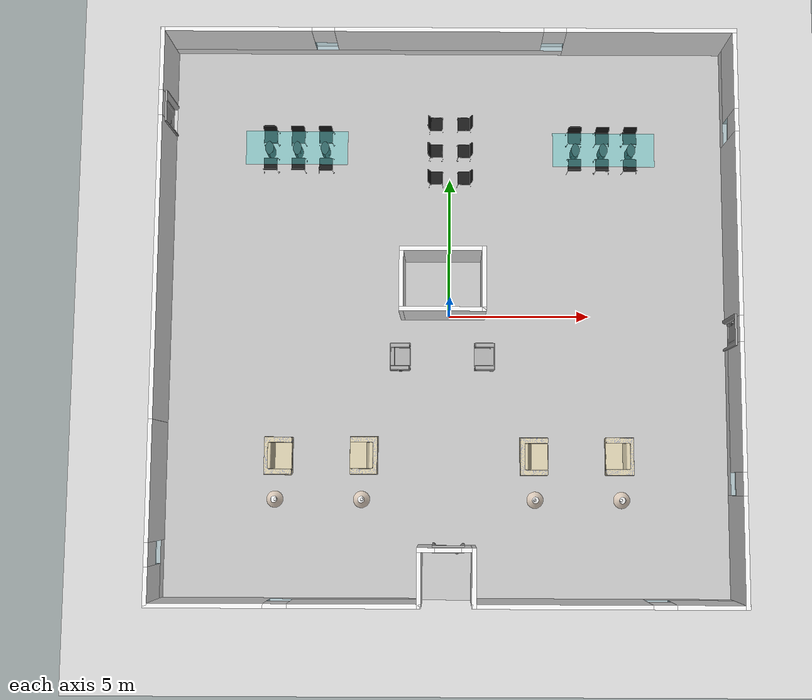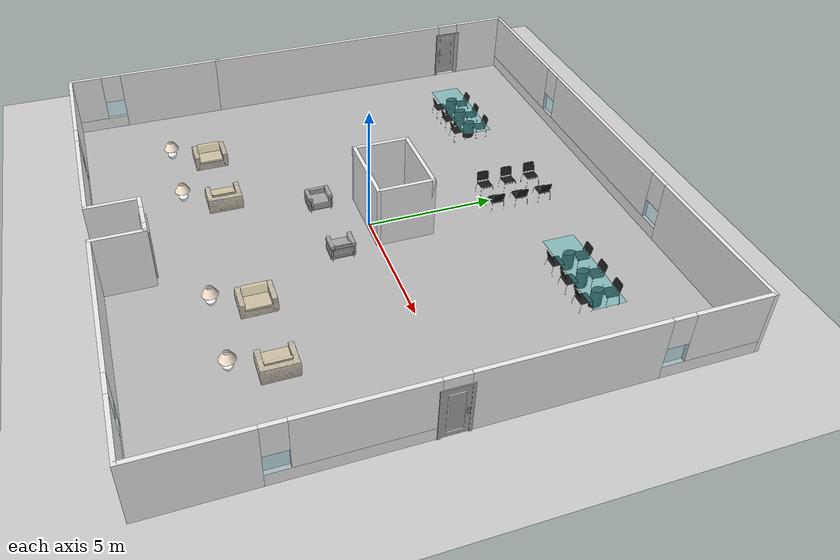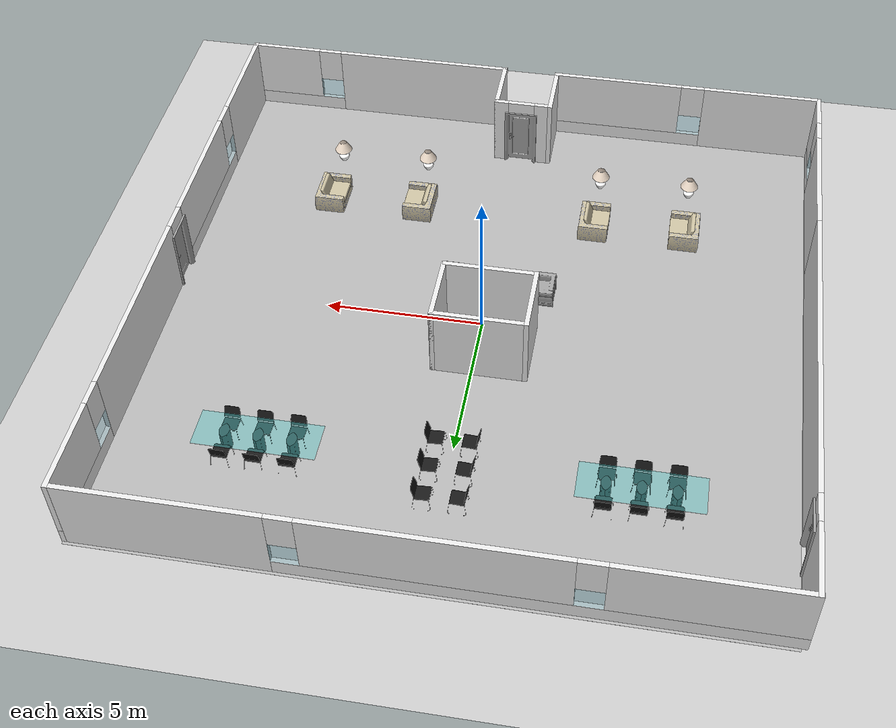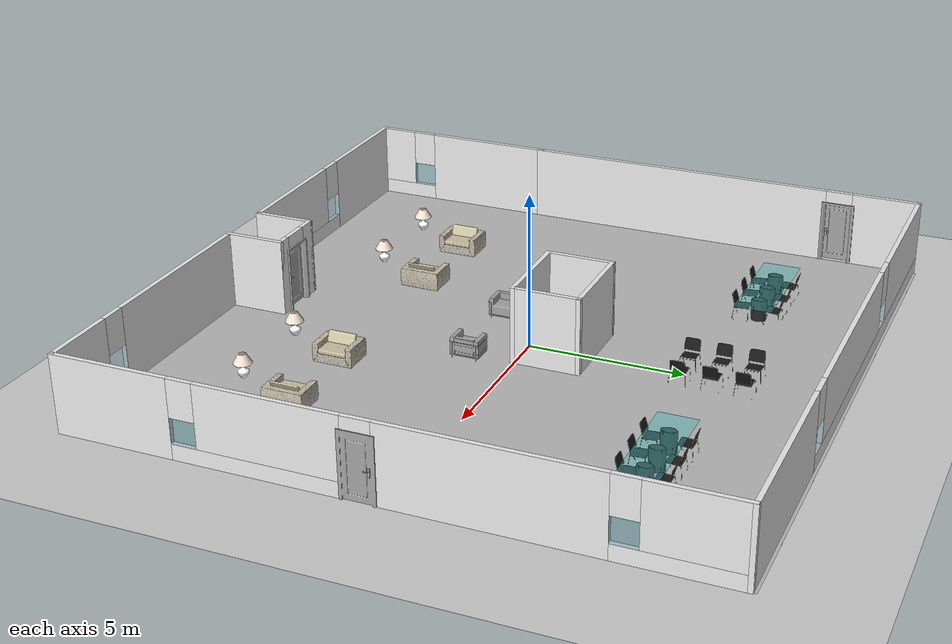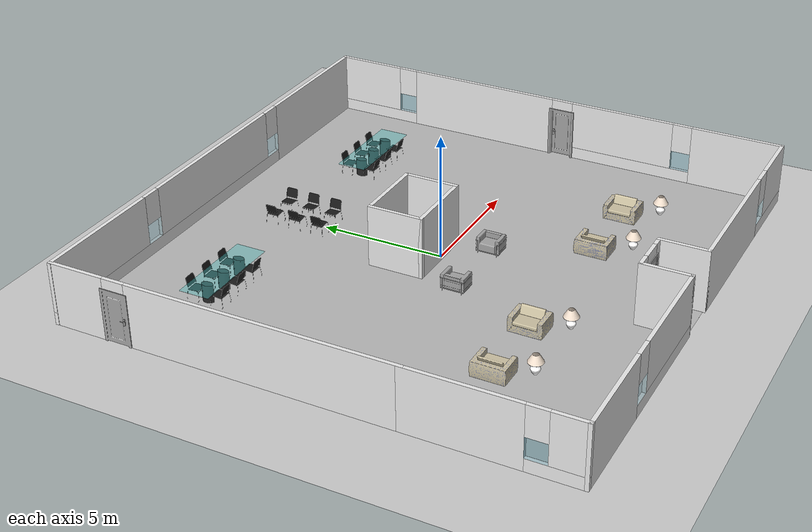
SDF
<sdf version="1.6">
 <world name="default">
  <scene><shadows>0</shadows><ambient>0.4 0.4 0.4 1</ambient><background>0.7 0.7 0.7 1</background></scene>
  <light name="sun" type="directional">
   <cast_shadows>0</cast_shadows>
   <pose>0 0 5 0 -0 0</pose>
   <diffuse>0.8 0.8 0.8 1</diffuse>
   <specular>0.1 0.1 0.1 1</specular>
   <attenuation>
    <range>1000</range>
    <constant>0.9</constant>
    <linear>0.01</linear>
    <quadratic>0.001</quadratic>
   </attenuation>
   <direction>-0.5 0.5 -1</direction>
  </light>
  <physics name="default_physics" default="0" type="ode">
   <max_step_size>0.001</max_step_size>
   <real_time_factor>1</real_time_factor>
   <real_time_update_rate>1000</real_time_update_rate>
  </physics>
  <scene><ambient>0.4 0.4 0.4 1</ambient><background>0.7 0.7 0.7 1</background><shadows>1</shadows></scene>
  <spherical_coordinates>
   <surface_model>EARTH_WGS84</surface_model>
   <latitude_deg>0</latitude_deg>
   <longitude_deg>0</longitude_deg>
   <elevation>0</elevation>
   <heading_deg>0</heading_deg>
  </spherical_coordinates>
  <model name="ground_plane">
   <static>1</static>
   <link name="link">
    <collision name="collision">
     <geometry><plane><normal>0 0 1</normal><size>100 100</size></plane></geometry>
     <surface><friction><ode><mu>1</mu><mu2>1</mu2></ode></friction></surface>
    </collision>
    <visual name="visual">
     <cast_shadows>0</cast_shadows>
     <geometry><plane><normal>0 0 1</normal><size>100 100</size></plane></geometry>
     <material>
      <script><uri>file://media/materials/scripts/gazebo.material</uri><name>Gazebo/Grey</name></script>
     </material>
    </visual>
    <velocity_decay><linear>0</linear><angular>0</angular></velocity_decay>
   </link>
  </model>
  <gravity>0 0 -9.8</gravity>
  <magnetic_field>6e-06 2.3e-05 -4.2e-05</magnetic_field>
  <atmosphere type="adiabatic"/>
  <model name="chair_set_1">
   <link name="link_16">
    <pose>0.07217 0.114259 -0.032065 0 -0 1.57</pose>
    <visual name="visual">
     <geometry><mesh><uri>model://chair_set_1/meshes/chair_frame.dae</uri><scale>1 1 1</scale></mesh></geometry>
     <material>
      <lighting>1</lighting>
      <ambient>0.3 0.3 0.3 1</ambient>
      <diffuse>0.7 0.7 0.7 1</diffuse>
      <specular>0.01 0.01 0.01 1</specular>
      <emissive>0 0 0 1</emissive>
      <shader type="vertex"><normal_map>__default__</normal_map></shader>
     </material>
    </visual>
    <collision name="collision">
     <geometry><mesh><uri>model://chair_set_1/meshes/chair_frame.dae</uri><scale>1 1 1</scale></mesh></geometry>
    </collision>
   </link>
   <link name="link_17">
    <pose>0.069192 0.1237 -0.032065 0 -0 1.57</pose>
    <visual name="visual">
     <geometry><mesh><uri>model://chair_set_1/meshes/chair_cushions.dae</uri><scale>1 1 1</scale></mesh></geometry>
     <material>
      <script>
       <uri>model://chair_set_1/materials/scripts</uri>
       <uri>model://chair_set_1/materials/textures</uri>
       <name>chair_set_1</name>
      </script>
     </material>
    </visual>
    <collision name="collision">
     <geometry><mesh><uri>model://chair_set_1/meshes/chair_cushions.dae</uri><scale>1 1 1</scale></mesh></geometry>
    </collision>
   </link>
   <link name="link_18">
    <pose>0.606963 -0.367766 -0.032065 0 -0 0</pose>
    <visual name="visual">
     <geometry>
      <mesh><uri>model://chair_set_1/meshes/sofa_cushions_back.dae</uri><scale>1 1 1</scale></mesh>
     </geometry>
     <material>
      <script>
       <uri>model://chair_set_1/materials/scripts</uri>
       <uri>model://chair_set_1/materials/textures</uri>
       <name>chair_set_1</name>
      </script>
     </material>
    </visual>
    <collision name="collision">
     <geometry>
      <mesh><uri>model://chair_set_1/meshes/sofa_cushions_back.dae</uri><scale>1 1 1</scale></mesh>
     </geometry>
    </collision>
   </link>
   <static>1</static>
   <pose>-1.75 -1.5 0 0 -0 1.57096</pose>
  </model>
  <model name="chair_set_1_0">
   <link name="link_16">
    <pose>0.07217 0.114259 -0.032065 0 -0 1.57</pose>
    <visual name="visual">
     <geometry><mesh><uri>model://chair_set_1/meshes/chair_frame.dae</uri><scale>1 1 1</scale></mesh></geometry>
     <material>
      <lighting>1</lighting>
      <ambient>0.3 0.3 0.3 1</ambient>
      <diffuse>0.7 0.7 0.7 1</diffuse>
      <specular>0.01 0.01 0.01 1</specular>
      <emissive>0 0 0 1</emissive>
      <shader type="vertex"><normal_map>__default__</normal_map></shader>
     </material>
    </visual>
    <collision name="collision">
     <geometry><mesh><uri>model://chair_set_1/meshes/chair_frame.dae</uri><scale>1 1 1</scale></mesh></geometry>
    </collision>
   </link>
   <link name="link_17">
    <pose>0.069192 0.1237 -0.032065 0 -0 1.57</pose>
    <visual name="visual">
     <geometry><mesh><uri>model://chair_set_1/meshes/chair_cushions.dae</uri><scale>1 1 1</scale></mesh></geometry>
     <material>
      <script>
       <uri>model://chair_set_1/materials/scripts</uri>
       <uri>model://chair_set_1/materials/textures</uri>
       <name>chair_set_1</name>
      </script>
     </material>
    </visual>
    <collision name="collision">
     <geometry><mesh><uri>model://chair_set_1/meshes/chair_cushions.dae</uri><scale>1 1 1</scale></mesh></geometry>
    </collision>
   </link>
   <link name="link_18">
    <pose>0.606963 -0.367766 -0.032065 0 -0 0</pose>
    <visual name="visual">
     <geometry>
      <mesh><uri>model://chair_set_1/meshes/sofa_cushions_back.dae</uri><scale>1 1 1</scale></mesh>
     </geometry>
     <material>
      <script>
       <uri>model://chair_set_1/materials/scripts</uri>
       <uri>model://chair_set_1/materials/textures</uri>
       <name>chair_set_1</name>
      </script>
     </material>
    </visual>
    <collision name="collision">
     <geometry>
      <mesh><uri>model://chair_set_1/meshes/sofa_cushions_back.dae</uri><scale>1 1 1</scale></mesh>
     </geometry>
    </collision>
   </link>
   <static>1</static>
   <pose>1.25 -1.5 0 0 0 -1.5708</pose>
  </model>
  <model name="chair_3">
   <link name="link_4">
    <pose>-0.282457 -0.259387 0 0 -0 0</pose>
    <visual name="visual">
     <geometry><mesh><uri>model://chair_3/meshes/model.dae</uri><scale>1 1 1</scale></mesh></geometry>
     <material>
      <lighting>1</lighting>
      <ambient>0 0 0 1</ambient>
      <diffuse>0.1 0.1 0.1 1</diffuse>
      <specular>0.01 0.01 0.01 1</specular>
      <emissive>0 0 0 1</emissive>
     </material>
    </visual>
    <collision name="collision">
     <geometry><mesh><uri>model://chair_3/meshes/model.dae</uri><scale>1 1 1</scale></mesh></geometry>
    </collision>
   </link>
   <static>1</static>
   <pose>4.5 6.5 0 0 -0 0</pose>
  </model>
  <model name="chair_3_clone">
   <link name="link_4">
    <pose>-0.282457 -0.259387 0 0 -0 0</pose>
    <visual name="visual">
     <geometry><mesh><uri>model://chair_3/meshes/model.dae</uri><scale>1 1 1</scale></mesh></geometry>
     <material>
      <lighting>1</lighting>
      <ambient>0 0 0 1</ambient>
      <diffuse>0.1 0.1 0.1 1</diffuse>
      <specular>0.01 0.01 0.01 1</specular>
      <emissive>0 0 0 1</emissive>
     </material>
    </visual>
    <collision name="collision">
     <geometry><mesh><uri>model://chair_3/meshes/model.dae</uri><scale>1 1 1</scale></mesh></geometry>
    </collision>
   </link>
   <static>1</static>
   <pose>5.5 6.5 0 0 -0 0</pose>
  </model>
  <model name="chair_3_clone_0">
   <link name="link_4">
    <pose>-0.282457 -0.259387 0 0 -0 0</pose>
    <visual name="visual">
     <geometry><mesh><uri>model://chair_3/meshes/model.dae</uri><scale>1 1 1</scale></mesh></geometry>
     <material>
      <lighting>1</lighting>
      <ambient>0 0 0 1</ambient>
      <diffuse>0.1 0.1 0.1 1</diffuse>
      <specular>0.01 0.01 0.01 1</specular>
      <emissive>0 0 0 1</emissive>
     </material>
    </visual>
    <collision name="collision">
     <geometry><mesh><uri>model://chair_3/meshes/model.dae</uri><scale>1 1 1</scale></mesh></geometry>
    </collision>
   </link>
   <static>1</static>
   <pose>6.5 6.5 0 0 -0 0</pose>
  </model>
  <model name="chair_3_clone_1">
   <link name="link_4">
    <pose>-0.282457 -0.259387 0 0 -0 0</pose>
    <visual name="visual">
     <geometry><mesh><uri>model://chair_3/meshes/model.dae</uri><scale>1 1 1</scale></mesh></geometry>
     <material>
      <lighting>1</lighting>
      <ambient>0 0 0 1</ambient>
      <diffuse>0.1 0.1 0.1 1</diffuse>
      <specular>0.01 0.01 0.01 1</specular>
      <emissive>0 0 0 1</emissive>
     </material>
    </visual>
    <collision name="collision">
     <geometry><mesh><uri>model://chair_3/meshes/model.dae</uri><scale>1 1 1</scale></mesh></geometry>
    </collision>
   </link>
   <static>1</static>
   <pose>6.5 5.5 0 0 -0 3.13584</pose>
  </model>
  <model name="chair_3_clone_1_clone">
   <link name="link_4">
    <pose>-0.282457 -0.259387 0 0 -0 0</pose>
    <visual name="visual">
     <geometry><mesh><uri>model://chair_3/meshes/model.dae</uri><scale>1 1 1</scale></mesh></geometry>
     <material>
      <lighting>1</lighting>
      <ambient>0 0 0 1</ambient>
      <diffuse>0.1 0.1 0.1 1</diffuse>
      <specular>0.01 0.01 0.01 1</specular>
      <emissive>0 0 0 1</emissive>
     </material>
    </visual>
    <collision name="collision">
     <geometry><mesh><uri>model://chair_3/meshes/model.dae</uri><scale>1 1 1</scale></mesh></geometry>
    </collision>
   </link>
   <static>1</static>
   <pose>5.5 5.5 0 0 -0 3.13584</pose>
  </model>
  <model name="chair_3_clone_1_clone_0">
   <link name="link_4">
    <pose>-0.282457 -0.259387 0 0 -0 0</pose>
    <visual name="visual">
     <geometry><mesh><uri>model://chair_3/meshes/model.dae</uri><scale>1 1 1</scale></mesh></geometry>
     <material>
      <lighting>1</lighting>
      <ambient>0 0 0 1</ambient>
      <diffuse>0.1 0.1 0.1 1</diffuse>
      <specular>0.01 0.01 0.01 1</specular>
      <emissive>0 0 0 1</emissive>
     </material>
    </visual>
    <collision name="collision">
     <geometry><mesh><uri>model://chair_3/meshes/model.dae</uri><scale>1 1 1</scale></mesh></geometry>
    </collision>
   </link>
   <static>1</static>
   <pose>4.5 5.5 0 0 -0 3.13584</pose>
  </model>
  <model name="chair_set_2">
   <link name="link_10">
    <pose>0.020402 -0.647852 0 0 -0 0</pose>
    <visual name="visual">
     <geometry><mesh><uri>model://chair_set_2/meshes/chair_frame.dae</uri><scale>1 1 1</scale></mesh></geometry>
     <material>
      <script>
       <uri>model://chair_set_2/materials/scripts</uri>
       <uri>model://chair_set_2/materials/textures</uri>
       <name>chair_set_2</name>
      </script>
     </material>
    </visual>
    <collision name="collision">
     <geometry><mesh><uri>model://chair_set_2/meshes/chair_frame.dae</uri><scale>1 1 1</scale></mesh></geometry>
    </collision>
   </link>
   <link name="link_11">
    <pose>0.015343 -0.628735 0 0 -0 0</pose>
    <visual name="visual">
     <geometry><mesh><uri>model://chair_set_2/meshes/chair_cushions.dae</uri><scale>1 1 1</scale></mesh></geometry>
     <material>
      <script>
       <uri>model://chair_set_2/materials/scripts</uri>
       <uri>model://chair_set_2/materials/textures</uri>
       <name>chair_set_2</name>
      </script>
     </material>
    </visual>
    <collision name="collision">
     <geometry><mesh><uri>model://chair_set_2/meshes/chair_cushions.dae</uri><scale>1 1 1</scale></mesh></geometry>
    </collision>
   </link>
   <static>1</static>
   <pose>-6 -5 0 0 -0 1.56766</pose>
  </model>
  <model name="chair_set_2_clone">
   <link name="link_10">
    <pose>0.020402 -0.647852 0 0 -0 0</pose>
    <visual name="visual">
     <geometry><mesh><uri>model://chair_set_2/meshes/chair_frame.dae</uri><scale>1 1 1</scale></mesh></geometry>
     <material>
      <script>
       <uri>model://chair_set_2/materials/scripts</uri>
       <uri>model://chair_set_2/materials/textures</uri>
       <name>chair_set_2</name>
      </script>
     </material>
    </visual>
    <collision name="collision">
     <geometry><mesh><uri>model://chair_set_2/meshes/chair_frame.dae</uri><scale>1 1 1</scale></mesh></geometry>
    </collision>
   </link>
   <link name="link_11">
    <pose>0.015343 -0.628735 0 0 -0 0</pose>
    <visual name="visual">
     <geometry><mesh><uri>model://chair_set_2/meshes/chair_cushions.dae</uri><scale>1 1 1</scale></mesh></geometry>
     <material>
      <script>
       <uri>model://chair_set_2/materials/scripts</uri>
       <uri>model://chair_set_2/materials/textures</uri>
       <name>chair_set_2</name>
      </script>
     </material>
    </visual>
    <collision name="collision">
     <geometry><mesh><uri>model://chair_set_2/meshes/chair_cushions.dae</uri><scale>1 1 1</scale></mesh></geometry>
    </collision>
   </link>
   <static>1</static>
   <pose>-3 -5 0 0 0 -1.57423</pose>
  </model>
  <model name="table_conference_3">
   <link name="link_6">
    <visual name="visual">
     <geometry><mesh><uri>model://table_conference_3/meshes/leg.dae</uri><scale>1 1 1</scale></mesh></geometry>
     <material>
      <script>
       <uri>model://table_conference_3/materials/scripts</uri>
       <uri>model://table_conference_3/materials/textures</uri>
       <name>table_conf_3</name>
      </script>
     </material>
    </visual>
    <collision name="collision">
     <geometry><mesh><uri>model://table_conference_3/meshes/leg.dae</uri><scale>1 1 1</scale></mesh></geometry>
    </collision>
   </link>
   <link name="link_7">
    <visual name="visual">
     <geometry><mesh><uri>model://table_conference_3/meshes/top.dae</uri><scale>1 1 1</scale></mesh></geometry>
     <material>
      <lighting>1</lighting>
      <ambient>0.278 0.776 0.776 1</ambient>
      <diffuse>0.278 0.776 0.776 1</diffuse>
      <specular>0.01 0.01 0.01 1</specular>
      <emissive>0 0 0 1</emissive>
      <shader type="vertex"><normal_map>__default__</normal_map></shader>
     </material>
     <transparency>0.6</transparency>
    </visual>
    <collision name="collision">
     <geometry><mesh><uri>model://table_conference_3/meshes/top.dae</uri><scale>1 1 1</scale></mesh></geometry>
    </collision>
   </link>
   <link name="link_8">
    <pose>0 1 0 0 -0 0</pose>
    <visual name="visual">
     <geometry><mesh><uri>model://table_conference_3/meshes/leg.dae</uri><scale>1 1 1</scale></mesh></geometry>
     <material>
      <script>
       <uri>model://table_conference_3/materials/scripts</uri>
       <uri>model://table_conference_3/materials/textures</uri>
       <name>table_conf_3</name>
      </script>
     </material>
    </visual>
    <collision name="collision">
     <geometry><mesh><uri>model://table_conference_3/meshes/leg.dae</uri><scale>1 1 1</scale></mesh></geometry>
    </collision>
   </link>
   <link name="link_9">
    <pose>0 -1 0 0 -0 0</pose>
    <visual name="visual">
     <geometry><mesh><uri>model://table_conference_3/meshes/leg.dae</uri><scale>1 1 1</scale></mesh></geometry>
     <material>
      <script>
       <uri>model://table_conference_3/materials/scripts</uri>
       <uri>model://table_conference_3/materials/textures</uri>
       <name>table_conf_3</name>
      </script>
     </material>
    </visual>
    <collision name="collision">
     <geometry><mesh><uri>model://table_conference_3/meshes/leg.dae</uri><scale>1 1 1</scale></mesh></geometry>
    </collision>
   </link>
   <static>1</static>
   <pose>5.5 6 -0.002256 0 0 -1.57202</pose>
  </model>
  <model name="lamp_table_large">
   <link name="link_20">
    <pose>-0.009128 0.000859 0 0 -0 0</pose>
    <visual name="visual">
     <geometry><mesh><uri>model://lamp_table_large/meshes/lamp_base.dae</uri><scale>1 1 1</scale></mesh></geometry>
     <material>
      <lighting>1</lighting>
      <ambient>1 1 1 1</ambient>
      <diffuse>1 1 1 1</diffuse>
      <specular>0.01 0.01 0.01 1</specular>
      <emissive>0 0 0 1</emissive>
     </material>
    </visual>
    <collision name="collision">
     <geometry><mesh><uri>model://lamp_table_large/meshes/lamp_base.dae</uri><scale>1 1 1</scale></mesh></geometry>
    </collision>
   </link>
   <link name="link_21">
    <pose>0.009129 -0.000859 0 0 -0 0</pose>
    <visual name="visual">
     <geometry><mesh><uri>model://lamp_table_large/meshes/lamp_head.dae</uri><scale>1 1 1</scale></mesh></geometry>
     <material>
      <lighting>1</lighting>
      <ambient>0.9568 0.8862 0.8156 1</ambient>
      <diffuse>0.9568 0.8862 0.8156 1</diffuse>
      <specular>0.01 0.01 0.01 1</specular>
      <emissive>0 0 0 1</emissive>
     </material>
    </visual>
    <collision name="collision">
     <geometry><mesh><uri>model://lamp_table_large/meshes/lamp_head.dae</uri><scale>1 1 1</scale></mesh></geometry>
    </collision>
   </link>
   <static>1</static>
   <pose>-6 -6.6 0.536836 0 -0 0</pose>
  </model>
  <model name="office_env_w_complete">
   <pose>-0.07705 -0.0907 0 0 -0 0</pose>
   <link name="Wall_10">
    <pose>-5.46873 -9.925 0 0 -0 0</pose>
    <visual name="Wall_10_Visual_0">
     <pose>-2.62812 0 1.25 0 -0 0</pose>
     <geometry><box><size>3.99376 0.15 2.5</size></box></geometry>
     <material>
      <script>
       <uri>model://office_env_w/materials/scripts</uri>
       <uri>model://office_env_w/materials/textures</uri>
       <name>wall_white</name>
      </script>
     </material>
     <meta><layer>0</layer></meta>
    </visual>
    <collision name="Wall_10_Collision_0">
     <geometry><box><size>3.99376 0.15 2.5</size></box></geometry>
     <pose>-2.62812 0 1.25 0 -0 0</pose>
    </collision>
    <visual name="Wall_10_Visual_1">
     <pose>1.99688 0 0.25 0 -0 0</pose>
     <geometry><box><size>5.25624 0.15 0.5</size></box></geometry>
     <material>
      <script>
       <uri>model://office_env_w/materials/scripts</uri>
       <uri>model://office_env_w/materials/textures</uri>
       <name>wall_white</name>
      </script>
     </material>
     <meta><layer>0</layer></meta>
    </visual>
    <collision name="Wall_10_Collision_1">
     <geometry><box><size>5.25624 0.15 0.5</size></box></geometry>
     <pose>1.99688 0 0.25 0 -0 0</pose>
    </collision>
    <visual name="Wall_10_Visual_2">
     <pose>2.39688 0 1.5 0 -0 0</pose>
     <geometry><box><size>4.45624 0.15 2</size></box></geometry>
     <material>
      <script>
       <uri>model://office_env_w/materials/scripts</uri>
       <uri>model://office_env_w/materials/textures</uri>
       <name>wall_white</name>
      </script>
     </material>
     <meta><layer>0</layer></meta>
    </visual>
    <collision name="Wall_10_Collision_2">
     <geometry><box><size>4.45624 0.15 2</size></box></geometry>
     <pose>2.39688 0 1.5 0 -0 0</pose>
    </collision>
    <visual name="Wall_10_Visual_3">
     <pose>-0.231239 0 1.9 0 -0 0</pose>
     <geometry><box><size>0.8 0.15 1.2</size></box></geometry>
     <material>
      <script>
       <uri>model://office_env_w/materials/scripts</uri>
       <uri>model://office_env_w/materials/textures</uri>
       <name>wall_white</name>
      </script>
     </material>
     <meta><layer>0</layer></meta>
    </visual>
    <collision name="Wall_10_Collision_3">
     <geometry><box><size>0.8 0.15 1.2</size></box></geometry>
     <pose>-0.231239 0 1.9 0 -0 0</pose>
    </collision>
   </link>
   <link name="window::link_2">
    <visual name="visual">
     <pose>0 0 0.9 0 -0 0</pose>
     <geometry><box><size>0.8 0.15 0.8</size></box></geometry>
     <material>
      <lighting>1</lighting>
      <ambient>0.1 0.5 0.6 1</ambient>
      <diffuse>0.1 0.5 0.6 1</diffuse>
      <specular>0.01 0.01 0.01 1</specular>
      <emissive>0 0 0 1</emissive>
     </material>
     <transparency>0.7</transparency>
    </visual>
    <collision name="collision">
     <pose>0 0 0.9 0 -0 0</pose>
     <geometry><box><size>0.8 0.15 0.8</size></box></geometry>
    </collision>
    <pose>-5.69997 -9.925 0 0 -0 0</pose>
   </link>
   <static>1</static>
   <link name="Wall_11">
    <collision name="Wall_11_Collision">
     <geometry><box><size>2 0.15 2.5</size></box></geometry>
     <pose>0 0 1.25 0 -0 0</pose>
    </collision>
    <visual name="Wall_11_Visual">
     <pose>0 0 1.25 0 -0 0</pose>
     <geometry><box><size>2 0.15 2.5</size></box></geometry>
     <material>
      <script>
       <uri>model://office_env_w/materials/scripts</uri>
       <uri>model://office_env_w/materials/textures</uri>
       <name>wall_white</name>
      </script>
     </material>
     <meta><layer>0</layer></meta>
    </visual>
    <pose>-0.918728 -9 0 0 -0 1.5708</pose>
   </link>
   <link name="Wall_12">
    <pose>0.006272 -8.075 0 0 -0 0</pose>
    <visual name="Wall_12_Visual_0">
     <pose>-0.695653 0 1.25 0 -0 0</pose>
     <geometry><box><size>0.608694 0.15 2.5</size></box></geometry>
     <material>
      <script>
       <uri>model://office_env_w/materials/scripts</uri>
       <uri>model://office_env_w/materials/textures</uri>
       <name>wall_white</name>
      </script>
     </material>
     <meta><layer>0</layer></meta>
    </visual>
    <collision name="Wall_12_Collision_0">
     <geometry><box><size>0.608694 0.15 2.5</size></box></geometry>
     <pose>-0.695653 0 1.25 0 -0 0</pose>
    </collision>
    <visual name="Wall_12_Visual_1">
     <pose>0.754347 0 1.25 0 -0 0</pose>
     <geometry><box><size>0.491306 0.15 2.5</size></box></geometry>
     <material>
      <script>
       <uri>model://office_env_w/materials/scripts</uri>
       <uri>model://office_env_w/materials/textures</uri>
       <name>wall_white</name>
      </script>
     </material>
     <meta><layer>0</layer></meta>
    </visual>
    <collision name="Wall_12_Collision_1">
     <geometry><box><size>0.491306 0.15 2.5</size></box></geometry>
     <pose>0.754347 0 1.25 0 -0 0</pose>
    </collision>
    <visual name="Wall_12_Visual_2">
     <pose>0.058694 0 2.25 0 -0 0</pose>
     <geometry><box><size>0.9 0.15 0.5</size></box></geometry>
     <material>
      <script>
       <uri>model://office_env_w/materials/scripts</uri>
       <uri>model://office_env_w/materials/textures</uri>
       <name>wall_white</name>
      </script>
     </material>
     <meta><layer>0</layer></meta>
    </visual>
    <collision name="Wall_12_Collision_2">
     <geometry><box><size>0.9 0.15 0.5</size></box></geometry>
     <pose>0.058694 0 2.25 0 -0 0</pose>
    </collision>
   </link>
   <link name="door_3d::link_1">
    <visual name="visual">
     <geometry><mesh><uri>model://door_3d/meshes/door_v2_door.dae</uri><scale>1 1 1</scale></mesh></geometry>
     <material>
      <script>
       <uri>model://door_3d/materials/scripts</uri>
       <uri>model://door_3d/materials/textures</uri>
       <name>door_3d</name>
      </script>
     </material>
    </visual>
    <collision name="collision">
     <geometry><mesh><uri>model://door_3d/meshes/door_v2_door.dae</uri><scale>1 1 1</scale></mesh></geometry>
    </collision>
    <pose>0.064966 -8.062 0 0 -0 0</pose>
   </link>
   <link name="door_3d::link_2">
    <visual name="visual">
     <geometry><mesh><uri>model://door_3d/meshes/door_v2_handle.dae</uri><scale>1 1 1</scale></mesh></geometry>
     <material>
      <script>
       <uri>model://door_3d/materials/scripts</uri>
       <uri>model://door_3d/materials/textures</uri>
       <name>door_handle</name>
      </script>
     </material>
    </visual>
    <collision name="collision">
     <geometry><mesh><uri>model://door_3d/meshes/door_v2_handle.dae</uri><scale>1 1 1</scale></mesh></geometry>
    </collision>
    <pose>0.064966 -8.062 0 0 -0 0</pose>
   </link>
   <static>1</static>
   <link name="Wall_15">
    <collision name="Wall_15_Collision">
     <geometry><box><size>2 0.15 2.5</size></box></geometry>
     <pose>0 0 1.25 0 -0 0</pose>
    </collision>
    <visual name="Wall_15_Visual">
     <pose>0 0 1.25 0 -0 0</pose>
     <geometry><box><size>2 0.15 2.5</size></box></geometry>
     <material>
      <script>
       <uri>model://office_env_w/materials/scripts</uri>
       <uri>model://office_env_w/materials/textures</uri>
       <name>wall_white</name>
      </script>
     </material>
     <meta><layer>0</layer></meta>
    </visual>
    <pose>0.931272 -9 0 0 0 -1.5708</pose>
   </link>
   <link name="Wall_16">
    <pose>5.48127 -9.925 0 0 -0 0</pose>
    <visual name="Wall_16_Visual_0">
     <pose>-1.61303 0 1.25 0 -0 0</pose>
     <geometry><box><size>6.02393 0.15 2.5</size></box></geometry>
     <material>
      <script>
       <uri>model://office_env_w/materials/scripts</uri>
       <uri>model://office_env_w/materials/textures</uri>
       <name>wall_white</name>
      </script>
     </material>
     <meta><layer>0</layer></meta>
    </visual>
    <collision name="Wall_16_Collision_0">
     <geometry><box><size>6.02393 0.15 2.5</size></box></geometry>
     <pose>-1.61303 0 1.25 0 -0 0</pose>
    </collision>
    <visual name="Wall_16_Visual_1">
     <pose>3.01197 0 0.25 0 -0 0</pose>
     <geometry><box><size>3.22607 0.15 0.5</size></box></geometry>
     <material>
      <script>
       <uri>model://office_env_w/materials/scripts</uri>
       <uri>model://office_env_w/materials/textures</uri>
       <name>wall_white</name>
      </script>
     </material>
     <meta><layer>0</layer></meta>
    </visual>
    <collision name="Wall_16_Collision_1">
     <geometry><box><size>3.22607 0.15 0.5</size></box></geometry>
     <pose>3.01197 0 0.25 0 -0 0</pose>
    </collision>
    <visual name="Wall_16_Visual_2">
     <pose>3.41197 0 1.5 0 -0 0</pose>
     <geometry><box><size>2.42607 0.15 2</size></box></geometry>
     <material>
      <script>
       <uri>model://office_env_w/materials/scripts</uri>
       <uri>model://office_env_w/materials/textures</uri>
       <name>wall_white</name>
      </script>
     </material>
     <meta><layer>0</layer></meta>
    </visual>
    <collision name="Wall_16_Collision_2">
     <geometry><box><size>2.42607 0.15 2</size></box></geometry>
     <pose>3.41197 0 1.5 0 -0 0</pose>
    </collision>
    <visual name="Wall_16_Visual_3">
     <pose>1.79893 0 1.9 0 -0 0</pose>
     <geometry><box><size>0.8 0.15 1.2</size></box></geometry>
     <material>
      <script>
       <uri>model://office_env_w/materials/scripts</uri>
       <uri>model://office_env_w/materials/textures</uri>
       <name>wall_white</name>
      </script>
     </material>
     <meta><layer>0</layer></meta>
    </visual>
    <collision name="Wall_16_Collision_3">
     <geometry><box><size>0.8 0.15 1.2</size></box></geometry>
     <pose>1.79893 0 1.9 0 -0 0</pose>
    </collision>
   </link>
   <link name="window::link_2">
    <visual name="visual">
     <pose>0 0 0.9 0 -0 0</pose>
     <geometry><box><size>0.8 0.15 0.8</size></box></geometry>
     <material>
      <lighting>1</lighting>
      <ambient>0.1 0.5 0.6 1</ambient>
      <diffuse>0.1 0.5 0.6 1</diffuse>
      <specular>0.01 0.01 0.01 1</specular>
      <emissive>0 0 0 1</emissive>
     </material>
     <transparency>0.7</transparency>
    </visual>
    <collision name="collision">
     <pose>0 0 0.9 0 -0 0</pose>
     <geometry><box><size>0.8 0.15 0.8</size></box></geometry>
    </collision>
    <pose>7.2802 -9.925 0 0 -0 0</pose>
   </link>
   <static>1</static>
   <link name="Wall_17">
    <pose>10.0313 0 0 0 -0 1.5708</pose>
    <visual name="Wall_17_Visual_0">
     <pose>-8.12184 0 1.25 0 -0 0</pose>
     <geometry><box><size>3.75631 0.15 2.5</size></box></geometry>
     <material>
      <script>
       <uri>model://office_env_w/materials/scripts</uri>
       <uri>model://office_env_w/materials/textures</uri>
       <name>wall_white</name>
      </script>
     </material>
     <meta><layer>0</layer></meta>
    </visual>
    <collision name="Wall_17_Collision_0">
     <geometry><box><size>3.75631 0.15 2.5</size></box></geometry>
     <pose>-8.12184 0 1.25 0 -0 0</pose>
    </collision>
    <visual name="Wall_17_Visual_1">
     <pose>3.09096 0 1.25 0 -0 0</pose>
     <geometry><box><size>6.45362 0.15 2.5</size></box></geometry>
     <material>
      <script>
       <uri>model://office_env_w/materials/scripts</uri>
       <uri>model://office_env_w/materials/textures</uri>
       <name>wall_white</name>
      </script>
     </material>
     <meta><layer>0</layer></meta>
    </visual>
    <collision name="Wall_17_Collision_1">
     <geometry><box><size>6.45362 0.15 2.5</size></box></geometry>
     <pose>3.09096 0 1.25 0 -0 0</pose>
    </collision>
    <visual name="Wall_17_Visual_2">
     <pose>-3.63977 0 0.25 0 -0 0</pose>
     <geometry><box><size>5.20784 0.15 0.5</size></box></geometry>
     <material>
      <script>
       <uri>model://office_env_w/materials/scripts</uri>
       <uri>model://office_env_w/materials/textures</uri>
       <name>wall_white</name>
      </script>
     </material>
     <meta><layer>0</layer></meta>
    </visual>
    <collision name="Wall_17_Collision_2">
     <geometry><box><size>5.20784 0.15 0.5</size></box></geometry>
     <pose>-3.63977 0 0.25 0 -0 0</pose>
    </collision>
    <visual name="Wall_17_Visual_3">
     <pose>8.15888 0 0.25 0 -0 0</pose>
     <geometry><box><size>3.68223 0.15 0.5</size></box></geometry>
     <material>
      <script>
       <uri>model://office_env_w/materials/scripts</uri>
       <uri>model://office_env_w/materials/textures</uri>
       <name>wall_white</name>
      </script>
     </material>
     <meta><layer>0</layer></meta>
    </visual>
    <collision name="Wall_17_Collision_3">
     <geometry><box><size>3.68223 0.15 0.5</size></box></geometry>
     <pose>8.15888 0 0.25 0 -0 0</pose>
    </collision>
    <visual name="Wall_17_Visual_4">
     <pose>-3.23977 0 1.5 0 -0 0</pose>
     <geometry><box><size>4.40784 0.15 2</size></box></geometry>
     <material>
      <script>
       <uri>model://office_env_w/materials/scripts</uri>
       <uri>model://office_env_w/materials/textures</uri>
       <name>wall_white</name>
      </script>
     </material>
     <meta><layer>0</layer></meta>
    </visual>
    <collision name="Wall_17_Collision_4">
     <geometry><box><size>4.40784 0.15 2</size></box></geometry>
     <pose>-3.23977 0 1.5 0 -0 0</pose>
    </collision>
    <visual name="Wall_17_Visual_5">
     <pose>-3.23977 0 1.5 0 -0 0</pose>
     <geometry><box><size>4.40784 0.15 2</size></box></geometry>
     <material>
      <script>
       <uri>model://office_env_w/materials/scripts</uri>
       <uri>model://office_env_w/materials/textures</uri>
       <name>wall_white</name>
      </script>
     </material>
     <meta><layer>0</layer></meta>
    </visual>
    <collision name="Wall_17_Collision_5">
     <geometry><box><size>4.40784 0.15 2</size></box></geometry>
     <pose>-3.23977 0 1.5 0 -0 0</pose>
    </collision>
    <visual name="Wall_17_Visual_6">
     <pose>8.55889 0 1.5 0 -0 0</pose>
     <geometry><box><size>2.88223 0.15 2</size></box></geometry>
     <material>
      <script>
       <uri>model://office_env_w/materials/scripts</uri>
       <uri>model://office_env_w/materials/textures</uri>
       <name>wall_white</name>
      </script>
     </material>
     <meta><layer>0</layer></meta>
    </visual>
    <collision name="Wall_17_Collision_6">
     <geometry><box><size>2.88223 0.15 2</size></box></geometry>
     <pose>8.55889 0 1.5 0 -0 0</pose>
    </collision>
    <visual name="Wall_17_Visual_7">
     <pose>-5.84369 0 1.9 0 -0 0</pose>
     <geometry><box><size>0.8 0.15 1.2</size></box></geometry>
     <material>
      <script>
       <uri>model://office_env_w/materials/scripts</uri>
       <uri>model://office_env_w/materials/textures</uri>
       <name>wall_white</name>
      </script>
     </material>
     <meta><layer>0</layer></meta>
    </visual>
    <collision name="Wall_17_Collision_7">
     <geometry><box><size>0.8 0.15 1.2</size></box></geometry>
     <pose>-5.84369 0 1.9 0 -0 0</pose>
    </collision>
    <visual name="Wall_17_Visual_8">
     <pose>6.71777 0 1.9 0 -0 0</pose>
     <geometry><box><size>0.8 0.15 1.2</size></box></geometry>
     <material>
      <script>
       <uri>model://office_env_w/materials/scripts</uri>
       <uri>model://office_env_w/materials/textures</uri>
       <name>wall_white</name>
      </script>
     </material>
     <meta><layer>0</layer></meta>
    </visual>
    <collision name="Wall_17_Collision_8">
     <geometry><box><size>0.8 0.15 1.2</size></box></geometry>
     <pose>6.71777 0 1.9 0 -0 0</pose>
    </collision>
    <visual name="Wall_17_Visual_9">
     <pose>-0.585848 0 2.25 0 -0 0</pose>
     <geometry><box><size>0.9 0.15 0.5</size></box></geometry>
     <material>
      <script>
       <uri>model://office_env_w/materials/scripts</uri>
       <uri>model://office_env_w/materials/textures</uri>
       <name>wall_white</name>
      </script>
     </material>
     <meta><layer>0</layer></meta>
    </visual>
    <collision name="Wall_17_Collision_9">
     <geometry><box><size>0.9 0.15 0.5</size></box></geometry>
     <pose>-0.585848 0 2.25 0 -0 0</pose>
    </collision>
    <visual name="Wall_17_Visual_10">
     <pose>-0.585848 0 2.25 0 -0 0</pose>
     <geometry><box><size>0.9 0.15 0.5</size></box></geometry>
     <material>
      <script>
       <uri>model://office_env_w/materials/scripts</uri>
       <uri>model://office_env_w/materials/textures</uri>
       <name>wall_white</name>
      </script>
     </material>
     <meta><layer>0</layer></meta>
    </visual>
    <collision name="Wall_17_Collision_10">
     <geometry><box><size>0.9 0.15 0.5</size></box></geometry>
     <pose>-0.585848 0 2.25 0 -0 0</pose>
    </collision>
   </link>
   <link name="door_3d::link_1">
    <visual name="visual">
     <geometry><mesh><uri>model://door_3d/meshes/door_v2_door.dae</uri><scale>1 1 1</scale></mesh></geometry>
     <material>
      <script>
       <uri>model://door_3d/materials/scripts</uri>
       <uri>model://door_3d/materials/textures</uri>
       <name>door_3d</name>
      </script>
     </material>
    </visual>
    <collision name="collision">
     <geometry><mesh><uri>model://door_3d/meshes/door_v2_door.dae</uri><scale>1 1 1</scale></mesh></geometry>
    </collision>
    <pose>10.018 -0.585848 0 0 -0 1.5708</pose>
   </link>
   <link name="door_3d::link_2">
    <visual name="visual">
     <geometry><mesh><uri>model://door_3d/meshes/door_v2_handle.dae</uri><scale>1 1 1</scale></mesh></geometry>
     <material>
      <script>
       <uri>model://door_3d/materials/scripts</uri>
       <uri>model://door_3d/materials/textures</uri>
       <name>door_handle</name>
      </script>
     </material>
    </visual>
    <collision name="collision">
     <geometry><mesh><uri>model://door_3d/meshes/door_v2_handle.dae</uri><scale>1 1 1</scale></mesh></geometry>
    </collision>
    <pose>10.018 -0.585848 0 0 -0 1.5708</pose>
   </link>
   <static>1</static>
   <link name="window::link_2">
    <visual name="visual">
     <pose>0 0 0.9 0 -0 0</pose>
     <geometry><box><size>0.8 0.15 0.8</size></box></geometry>
     <material>
      <lighting>1</lighting>
      <ambient>0.1 0.5 0.6 1</ambient>
      <diffuse>0.1 0.5 0.6 1</diffuse>
      <specular>0.01 0.01 0.01 1</specular>
      <emissive>0 0 0 1</emissive>
     </material>
     <transparency>0.7</transparency>
    </visual>
    <collision name="collision">
     <pose>0 0 0.9 0 -0 0</pose>
     <geometry><box><size>0.8 0.15 0.8</size></box></geometry>
    </collision>
    <pose>10.0313 -5.84369 0 0 -0 1.5708</pose>
   </link>
   <static>1</static>
   <link name="window::link_2">
    <visual name="visual">
     <pose>0 0 0.9 0 -0 0</pose>
     <geometry><box><size>0.8 0.15 0.8</size></box></geometry>
     <material>
      <lighting>1</lighting>
      <ambient>0.1 0.5 0.6 1</ambient>
      <diffuse>0.1 0.5 0.6 1</diffuse>
      <specular>0.01 0.01 0.01 1</specular>
      <emissive>0 0 0 1</emissive>
     </material>
     <transparency>0.7</transparency>
    </visual>
    <collision name="collision">
     <pose>0 0 0.9 0 -0 0</pose>
     <geometry><box><size>0.8 0.15 0.8</size></box></geometry>
    </collision>
    <pose>10.0313 6.71777 0 0 -0 1.5708</pose>
   </link>
   <static>1</static>
   <link name="Wall_19">
    <pose>-0 9.925 0 0 -0 3.14159</pose>
    <visual name="Wall_19_Visual_0">
     <pose>-7.12533 0 1.25 0 -0 0</pose>
     <geometry><box><size>5.96188 0.15 2.5</size></box></geometry>
     <material>
      <script>
       <uri>model://office_env_w/materials/scripts</uri>
       <uri>model://office_env_w/materials/textures</uri>
       <name>wall_white</name>
      </script>
     </material>
     <meta><layer>0</layer></meta>
    </visual>
    <collision name="Wall_19_Collision_0">
     <geometry><box><size>5.96188 0.15 2.5</size></box></geometry>
     <pose>-7.12533 0 1.25 0 -0 0</pose>
    </collision>
    <visual name="Wall_19_Visual_1">
     <pose>2.98094 0 0.25 0 -0 0</pose>
     <geometry><box><size>14.2507 0.15 0.5</size></box></geometry>
     <material>
      <script>
       <uri>model://office_env_w/materials/scripts</uri>
       <uri>model://office_env_w/materials/textures</uri>
       <name>wall_white</name>
      </script>
     </material>
     <meta><layer>0</layer></meta>
    </visual>
    <collision name="Wall_19_Collision_1">
     <geometry><box><size>14.2507 0.15 0.5</size></box></geometry>
     <pose>2.98094 0 0.25 0 -0 0</pose>
    </collision>
    <visual name="Wall_19_Visual_2">
     <pose>0.326454 0 1.5 0 -0 0</pose>
     <geometry><box><size>7.34169 0.15 2</size></box></geometry>
     <material>
      <script>
       <uri>model://office_env_w/materials/scripts</uri>
       <uri>model://office_env_w/materials/textures</uri>
       <name>wall_white</name>
      </script>
     </material>
     <meta><layer>0</layer></meta>
    </visual>
    <collision name="Wall_19_Collision_2">
     <geometry><box><size>7.34169 0.15 2</size></box></geometry>
     <pose>0.326454 0 1.5 0 -0 0</pose>
    </collision>
    <visual name="Wall_19_Visual_3">
     <pose>7.45179 0 1.5 0 -0 0</pose>
     <geometry><box><size>5.30898 0.15 2</size></box></geometry>
     <material>
      <script>
       <uri>model://office_env_w/materials/scripts</uri>
       <uri>model://office_env_w/materials/textures</uri>
       <name>wall_white</name>
      </script>
     </material>
     <meta><layer>0</layer></meta>
    </visual>
    <collision name="Wall_19_Collision_3">
     <geometry><box><size>5.30898 0.15 2</size></box></geometry>
     <pose>7.45179 0 1.5 0 -0 0</pose>
    </collision>
    <visual name="Wall_19_Visual_4">
     <pose>-3.74439 0 1.9 0 -0 0</pose>
     <geometry><box><size>0.8 0.15 1.2</size></box></geometry>
     <material>
      <script>
       <uri>model://office_env_w/materials/scripts</uri>
       <uri>model://office_env_w/materials/textures</uri>
       <name>wall_white</name>
      </script>
     </material>
     <meta><layer>0</layer></meta>
    </visual>
    <collision name="Wall_19_Collision_4">
     <geometry><box><size>0.8 0.15 1.2</size></box></geometry>
     <pose>-3.74439 0 1.9 0 -0 0</pose>
    </collision>
    <visual name="Wall_19_Visual_5">
     <pose>4.3973 0 1.9 0 -0 0</pose>
     <geometry><box><size>0.8 0.15 1.2</size></box></geometry>
     <material>
      <script>
       <uri>model://office_env_w/materials/scripts</uri>
       <uri>model://office_env_w/materials/textures</uri>
       <name>wall_white</name>
      </script>
     </material>
     <meta><layer>0</layer></meta>
    </visual>
    <collision name="Wall_19_Collision_5">
     <geometry><box><size>0.8 0.15 1.2</size></box></geometry>
     <pose>4.3973 0 1.9 0 -0 0</pose>
    </collision>
   </link>
   <link name="window::link_2">
    <visual name="visual">
     <pose>0 0 0.9 0 -0 0</pose>
     <geometry><box><size>0.8 0.15 0.8</size></box></geometry>
     <material>
      <lighting>1</lighting>
      <ambient>0.1 0.5 0.6 1</ambient>
      <diffuse>0.1 0.5 0.6 1</diffuse>
      <specular>0.01 0.01 0.01 1</specular>
      <emissive>0 0 0 1</emissive>
     </material>
     <transparency>0.7</transparency>
    </visual>
    <collision name="collision">
     <pose>0 0 0.9 0 -0 0</pose>
     <geometry><box><size>0.8 0.15 0.8</size></box></geometry>
    </collision>
    <pose>3.74439 9.925 0 0 -0 3.14159</pose>
   </link>
   <static>1</static>
   <link name="window::link_2">
    <visual name="visual">
     <pose>0 0 0.9 0 -0 0</pose>
     <geometry><box><size>0.8 0.15 0.8</size></box></geometry>
     <material>
      <lighting>1</lighting>
      <ambient>0.1 0.5 0.6 1</ambient>
      <diffuse>0.1 0.5 0.6 1</diffuse>
      <specular>0.01 0.01 0.01 1</specular>
      <emissive>0 0 0 1</emissive>
     </material>
     <transparency>0.7</transparency>
    </visual>
    <collision name="collision">
     <pose>0 0 0.9 0 -0 0</pose>
     <geometry><box><size>0.8 0.15 0.8</size></box></geometry>
    </collision>
    <pose>-4.3973 9.925 0 0 -0 3.14159</pose>
   </link>
   <static>1</static>
   <link name="Wall_2">
    <pose>-10.0187 -6.75 0 0 0 -1.5708</pose>
    <visual name="Wall_2_Visual_0">
     <pose>-1.06854 0 1.25 0 -0 0</pose>
     <geometry><box><size>4.36293 0.15 2.5</size></box></geometry>
     <material>
      <script>
       <uri>model://office_env_w/materials/scripts</uri>
       <uri>model://office_env_w/materials/textures</uri>
       <name>wall_white</name>
      </script>
     </material>
     <meta><layer>0</layer></meta>
    </visual>
    <collision name="Wall_2_Collision_0">
     <geometry><box><size>4.36293 0.15 2.5</size></box></geometry>
     <pose>-1.06854 0 1.25 0 -0 0</pose>
    </collision>
    <visual name="Wall_2_Visual_1">
     <pose>2.18147 0 0.25 0 -0 0</pose>
     <geometry><box><size>2.13707 0.15 0.5</size></box></geometry>
     <material>
      <script>
       <uri>model://office_env_w/materials/scripts</uri>
       <uri>model://office_env_w/materials/textures</uri>
       <name>wall_white</name>
      </script>
     </material>
     <meta><layer>0</layer></meta>
    </visual>
    <collision name="Wall_2_Collision_1">
     <geometry><box><size>2.13707 0.15 0.5</size></box></geometry>
     <pose>2.18147 0 0.25 0 -0 0</pose>
    </collision>
    <visual name="Wall_2_Visual_2">
     <pose>2.58147 0 1.5 0 -0 0</pose>
     <geometry><box><size>1.33707 0.15 2</size></box></geometry>
     <material>
      <script>
       <uri>model://office_env_w/materials/scripts</uri>
       <uri>model://office_env_w/materials/textures</uri>
       <name>wall_white</name>
      </script>
     </material>
     <meta><layer>0</layer></meta>
    </visual>
    <collision name="Wall_2_Collision_2">
     <geometry><box><size>1.33707 0.15 2</size></box></geometry>
     <pose>2.58147 0 1.5 0 -0 0</pose>
    </collision>
    <visual name="Wall_2_Visual_3">
     <pose>1.51293 0 1.9 0 -0 0</pose>
     <geometry><box><size>0.8 0.15 1.2</size></box></geometry>
     <material>
      <script>
       <uri>model://office_env_w/materials/scripts</uri>
       <uri>model://office_env_w/materials/textures</uri>
       <name>wall_white</name>
      </script>
     </material>
     <meta><layer>0</layer></meta>
    </visual>
    <collision name="Wall_2_Collision_3">
     <geometry><box><size>0.8 0.15 1.2</size></box></geometry>
     <pose>1.51293 0 1.9 0 -0 0</pose>
    </collision>
   </link>
   <link name="window::link_2">
    <visual name="visual">
     <pose>0 0 0.9 0 -0 0</pose>
     <geometry><box><size>0.8 0.15 0.8</size></box></geometry>
     <material>
      <lighting>1</lighting>
      <ambient>0.1 0.5 0.6 1</ambient>
      <diffuse>0.1 0.5 0.6 1</diffuse>
      <specular>0.01 0.01 0.01 1</specular>
      <emissive>0 0 0 1</emissive>
     </material>
     <transparency>0.7</transparency>
    </visual>
    <collision name="collision">
     <pose>0 0 0.9 0 -0 0</pose>
     <geometry><box><size>0.8 0.15 0.8</size></box></geometry>
    </collision>
    <pose>-10.0187 -8.26293 0 0 0 -1.57</pose>
   </link>
   <static>1</static>
   <link name="Wall_20">
    <pose>-10.018 3.125 0 0 0 -1.5708</pose>
    <visual name="Wall_20_Visual_0">
     <pose>-5.73803 0 1.25 0 -0 0</pose>
     <geometry><box><size>2.27394 0.15 2.5</size></box></geometry>
     <material>
      <script>
       <uri>model://office_env_w/materials/scripts</uri>
       <uri>model://office_env_w/materials/textures</uri>
       <name>wall_white</name>
      </script>
     </material>
     <meta><layer>0</layer></meta>
    </visual>
    <collision name="Wall_20_Collision_0">
     <geometry><box><size>2.27394 0.15 2.5</size></box></geometry>
     <pose>-5.73803 0 1.25 0 -0 0</pose>
    </collision>
    <visual name="Wall_20_Visual_1">
     <pose>1.58697 0 1.25 0 -0 0</pose>
     <geometry><box><size>10.5761 0.15 2.5</size></box></geometry>
     <material>
      <script>
       <uri>model://office_env_w/materials/scripts</uri>
       <uri>model://office_env_w/materials/textures</uri>
       <name>wall_white</name>
      </script>
     </material>
     <meta><layer>0</layer></meta>
    </visual>
    <collision name="Wall_20_Collision_1">
     <geometry><box><size>10.5761 0.15 2.5</size></box></geometry>
     <pose>1.58697 0 1.25 0 -0 0</pose>
    </collision>
    <visual name="Wall_20_Visual_2">
     <pose>-4.15106 0 2.25 0 -0 0</pose>
     <geometry><box><size>0.9 0.15 0.5</size></box></geometry>
     <material>
      <script>
       <uri>model://office_env_w/materials/scripts</uri>
       <uri>model://office_env_w/materials/textures</uri>
       <name>wall_white</name>
      </script>
     </material>
     <meta><layer>0</layer></meta>
    </visual>
    <collision name="Wall_20_Collision_2">
     <geometry><box><size>0.9 0.15 0.5</size></box></geometry>
     <pose>-4.15106 0 2.25 0 -0 0</pose>
    </collision>
   </link>
   <link name="door_3d::link_1">
    <visual name="visual">
     <geometry><mesh><uri>model://door_3d/meshes/door_v2_door.dae</uri><scale>1 1 1</scale></mesh></geometry>
     <material>
      <script>
       <uri>model://door_3d/materials/scripts</uri>
       <uri>model://door_3d/materials/textures</uri>
       <name>door_3d</name>
      </script>
     </material>
    </visual>
    <collision name="collision">
     <geometry><mesh><uri>model://door_3d/meshes/door_v2_door.dae</uri><scale>1 1 1</scale></mesh></geometry>
    </collision>
    <pose>-10.005 7.27606 0 0 0 -1.5708</pose>
   </link>
   <link name="door_3d::link_2">
    <visual name="visual">
     <geometry><mesh><uri>model://door_3d/meshes/door_v2_handle.dae</uri><scale>1 1 1</scale></mesh></geometry>
     <material>
      <script>
       <uri>model://door_3d/materials/scripts</uri>
       <uri>model://door_3d/materials/textures</uri>
       <name>door_handle</name>
      </script>
     </material>
    </visual>
    <collision name="collision">
     <geometry><mesh><uri>model://door_3d/meshes/door_v2_handle.dae</uri><scale>1 1 1</scale></mesh></geometry>
    </collision>
    <pose>-10.005 7.27606 0 0 0 -1.5708</pose>
   </link>
   <static>1</static>
   <link name="Wall_22">
    <collision name="Wall_22_Collision">
     <geometry><box><size>3 0.15 2.5</size></box></geometry>
     <pose>0 0 1.25 0 -0 0</pose>
    </collision>
    <visual name="Wall_22_Visual">
     <pose>0 0 1.25 0 -0 0</pose>
     <geometry><box><size>3 0.15 2.5</size></box></geometry>
     <material>
      <script>
       <uri>model://office_env_w/materials/scripts</uri>
       <uri>model://office_env_w/materials/textures</uri>
       <name>wall_white</name>
      </script>
     </material>
     <meta><layer>0</layer></meta>
    </visual>
    <pose>-0.163956 0.04737 0 0 -0 3.14159</pose>
   </link>
   <link name="Wall_23">
    <collision name="Wall_23_Collision">
     <geometry><box><size>2.25 0.15 2.5</size></box></geometry>
     <pose>0 0 1.25 0 -0 0</pose>
    </collision>
    <visual name="Wall_23_Visual">
     <pose>0 0 1.25 0 -0 0</pose>
     <geometry><box><size>2.25 0.15 2.5</size></box></geometry>
     <material>
      <script>
       <uri>model://office_env_w/materials/scripts</uri>
       <uri>model://office_env_w/materials/textures</uri>
       <name>wall_white</name>
      </script>
     </material>
     <meta><layer>0</layer></meta>
    </visual>
    <pose>-1.58896 1.09737 0 0 -0 1.5708</pose>
   </link>
   <link name="Wall_24">
    <collision name="Wall_24_Collision">
     <geometry><box><size>3 0.15 2.5</size></box></geometry>
     <pose>0 0 1.25 0 -0 0</pose>
    </collision>
    <visual name="Wall_24_Visual">
     <pose>0 0 1.25 0 -0 0</pose>
     <geometry><box><size>3 0.15 2.5</size></box></geometry>
     <material>
      <script>
       <uri>model://office_env_w/materials/scripts</uri>
       <uri>model://office_env_w/materials/textures</uri>
       <name>wall_white</name>
      </script>
     </material>
     <meta><layer>0</layer></meta>
    </visual>
    <pose>-0.163956 2.14737 0 0 -0 0</pose>
   </link>
   <link name="Wall_25">
    <collision name="Wall_25_Collision">
     <geometry><box><size>2.25 0.15 2.5</size></box></geometry>
     <pose>0 0 1.25 0 -0 0</pose>
    </collision>
    <visual name="Wall_25_Visual">
     <pose>0 0 1.25 0 -0 0</pose>
     <geometry><box><size>2.25 0.15 2.5</size></box></geometry>
     <material>
      <script>
       <uri>model://office_env_w/materials/scripts</uri>
       <uri>model://office_env_w/materials/textures</uri>
       <name>wall_white</name>
      </script>
     </material>
     <meta><layer>0</layer></meta>
    </visual>
    <pose>1.26104 1.09737 0 0 0 -1.5708</pose>
   </link>
   <static>1</static>
  </model>
  <model name="table_conference_3_0">
   <link name="link_6">
    <visual name="visual">
     <geometry><mesh><uri>model://table_conference_3/meshes/leg.dae</uri><scale>1 1 1</scale></mesh></geometry>
     <material>
      <script>
       <uri>model://table_conference_3/materials/scripts</uri>
       <uri>model://table_conference_3/materials/textures</uri>
       <name>table_conf_3</name>
      </script>
     </material>
    </visual>
    <collision name="collision">
     <geometry><mesh><uri>model://table_conference_3/meshes/leg.dae</uri><scale>1 1 1</scale></mesh></geometry>
    </collision>
   </link>
   <link name="link_7">
    <visual name="visual">
     <geometry><mesh><uri>model://table_conference_3/meshes/top.dae</uri><scale>1 1 1</scale></mesh></geometry>
     <material>
      <lighting>1</lighting>
      <ambient>0.278 0.776 0.776 1</ambient>
      <diffuse>0.278 0.776 0.776 1</diffuse>
      <specular>0.01 0.01 0.01 1</specular>
      <emissive>0 0 0 1</emissive>
      <shader type="vertex"><normal_map>__default__</normal_map></shader>
     </material>
     <transparency>0.6</transparency>
    </visual>
    <collision name="collision">
     <geometry><mesh><uri>model://table_conference_3/meshes/top.dae</uri><scale>1 1 1</scale></mesh></geometry>
    </collision>
   </link>
   <link name="link_8">
    <pose>0 1 0 0 -0 0</pose>
    <visual name="visual">
     <geometry><mesh><uri>model://table_conference_3/meshes/leg.dae</uri><scale>1 1 1</scale></mesh></geometry>
     <material>
      <script>
       <uri>model://table_conference_3/materials/scripts</uri>
       <uri>model://table_conference_3/materials/textures</uri>
       <name>table_conf_3</name>
      </script>
     </material>
    </visual>
    <collision name="collision">
     <geometry><mesh><uri>model://table_conference_3/meshes/leg.dae</uri><scale>1 1 1</scale></mesh></geometry>
    </collision>
   </link>
   <link name="link_9">
    <pose>0 -1 0 0 -0 0</pose>
    <visual name="visual">
     <geometry><mesh><uri>model://table_conference_3/meshes/leg.dae</uri><scale>1 1 1</scale></mesh></geometry>
     <material>
      <script>
       <uri>model://table_conference_3/materials/scripts</uri>
       <uri>model://table_conference_3/materials/textures</uri>
       <name>table_conf_3</name>
      </script>
     </material>
    </visual>
    <collision name="collision">
     <geometry><mesh><uri>model://table_conference_3/meshes/leg.dae</uri><scale>1 1 1</scale></mesh></geometry>
    </collision>
   </link>
   <static>1</static>
   <pose>-5.5 6 0 0 -0 1.5708</pose>
  </model>
  <model name="chair_3_0">
   <link name="link_4">
    <pose>-0.282457 -0.259387 0 0 -0 0</pose>
    <visual name="visual">
     <geometry><mesh><uri>model://chair_3/meshes/model.dae</uri><scale>1 1 1</scale></mesh></geometry>
     <material>
      <lighting>1</lighting>
      <ambient>0 0 0 1</ambient>
      <diffuse>0.1 0.1 0.1 1</diffuse>
      <specular>0.01 0.01 0.01 1</specular>
      <emissive>0 0 0 1</emissive>
     </material>
    </visual>
    <collision name="collision">
     <geometry><mesh><uri>model://chair_3/meshes/model.dae</uri><scale>1 1 1</scale></mesh></geometry>
    </collision>
   </link>
   <static>1</static>
   <pose>-6.5 6.5 0 0 -0 0</pose>
  </model>
  <model name="chair_3_1">
   <link name="link_4">
    <pose>-0.282457 -0.259387 0 0 -0 0</pose>
    <visual name="visual">
     <geometry><mesh><uri>model://chair_3/meshes/model.dae</uri><scale>1 1 1</scale></mesh></geometry>
     <material>
      <lighting>1</lighting>
      <ambient>0 0 0 1</ambient>
      <diffuse>0.1 0.1 0.1 1</diffuse>
      <specular>0.01 0.01 0.01 1</specular>
      <emissive>0 0 0 1</emissive>
     </material>
    </visual>
    <collision name="collision">
     <geometry><mesh><uri>model://chair_3/meshes/model.dae</uri><scale>1 1 1</scale></mesh></geometry>
    </collision>
   </link>
   <static>1</static>
   <pose>-5.5 6.5 0 0 -0 0</pose>
  </model>
  <model name="chair_3_2">
   <link name="link_4">
    <pose>-0.282457 -0.259387 0 0 -0 0</pose>
    <visual name="visual">
     <geometry><mesh><uri>model://chair_3/meshes/model.dae</uri><scale>1 1 1</scale></mesh></geometry>
     <material>
      <lighting>1</lighting>
      <ambient>0 0 0 1</ambient>
      <diffuse>0.1 0.1 0.1 1</diffuse>
      <specular>0.01 0.01 0.01 1</specular>
      <emissive>0 0 0 1</emissive>
     </material>
    </visual>
    <collision name="collision">
     <geometry><mesh><uri>model://chair_3/meshes/model.dae</uri><scale>1 1 1</scale></mesh></geometry>
    </collision>
   </link>
   <static>1</static>
   <pose>-4.5 6.5 0 0 -0 0</pose>
  </model>
  <model name="chair_3_3">
   <link name="link_4">
    <pose>-0.282457 -0.259387 0 0 -0 0</pose>
    <visual name="visual">
     <geometry><mesh><uri>model://chair_3/meshes/model.dae</uri><scale>1 1 1</scale></mesh></geometry>
     <material>
      <lighting>1</lighting>
      <ambient>0 0 0 1</ambient>
      <diffuse>0.1 0.1 0.1 1</diffuse>
      <specular>0.01 0.01 0.01 1</specular>
      <emissive>0 0 0 1</emissive>
     </material>
    </visual>
    <collision name="collision">
     <geometry><mesh><uri>model://chair_3/meshes/model.dae</uri><scale>1 1 1</scale></mesh></geometry>
    </collision>
   </link>
   <static>1</static>
   <pose>-0.500001 7 0 0 -0 1.5708</pose>
  </model>
  <model name="chair_3_4">
   <link name="link_4">
    <pose>-0.282457 -0.259387 0 0 -0 0</pose>
    <visual name="visual">
     <geometry><mesh><uri>model://chair_3/meshes/model.dae</uri><scale>1 1 1</scale></mesh></geometry>
     <material>
      <lighting>1</lighting>
      <ambient>0 0 0 1</ambient>
      <diffuse>0.1 0.1 0.1 1</diffuse>
      <specular>0.01 0.01 0.01 1</specular>
      <emissive>0 0 0 1</emissive>
     </material>
    </visual>
    <collision name="collision">
     <geometry><mesh><uri>model://chair_3/meshes/model.dae</uri><scale>1 1 1</scale></mesh></geometry>
    </collision>
   </link>
   <static>1</static>
   <pose>-0.500001 6 0 0 -0 1.5708</pose>
  </model>
  <model name="chair_3_5">
   <link name="link_4">
    <pose>-0.282457 -0.259387 0 0 -0 0</pose>
    <visual name="visual">
     <geometry><mesh><uri>model://chair_3/meshes/model.dae</uri><scale>1 1 1</scale></mesh></geometry>
     <material>
      <lighting>1</lighting>
      <ambient>0 0 0 1</ambient>
      <diffuse>0.1 0.1 0.1 1</diffuse>
      <specular>0.01 0.01 0.01 1</specular>
      <emissive>0 0 0 1</emissive>
     </material>
    </visual>
    <collision name="collision">
     <geometry><mesh><uri>model://chair_3/meshes/model.dae</uri><scale>1 1 1</scale></mesh></geometry>
    </collision>
   </link>
   <static>1</static>
   <pose>-6.5 5.5 0 0 -0 3.14</pose>
  </model>
  <model name="chair_3_6">
   <link name="link_4">
    <pose>-0.282457 -0.259387 0 0 -0 0</pose>
    <visual name="visual">
     <geometry><mesh><uri>model://chair_3/meshes/model.dae</uri><scale>1 1 1</scale></mesh></geometry>
     <material>
      <lighting>1</lighting>
      <ambient>0 0 0 1</ambient>
      <diffuse>0.1 0.1 0.1 1</diffuse>
      <specular>0.01 0.01 0.01 1</specular>
      <emissive>0 0 0 1</emissive>
     </material>
    </visual>
    <collision name="collision">
     <geometry><mesh><uri>model://chair_3/meshes/model.dae</uri><scale>1 1 1</scale></mesh></geometry>
    </collision>
   </link>
   <static>1</static>
   <pose>-5.5 5.5 0 0 -0 3.14</pose>
  </model>
  <model name="chair_3_7">
   <link name="link_4">
    <pose>-0.282457 -0.259387 0 0 -0 0</pose>
    <visual name="visual">
     <geometry><mesh><uri>model://chair_3/meshes/model.dae</uri><scale>1 1 1</scale></mesh></geometry>
     <material>
      <lighting>1</lighting>
      <ambient>0 0 0 1</ambient>
      <diffuse>0.1 0.1 0.1 1</diffuse>
      <specular>0.01 0.01 0.01 1</specular>
      <emissive>0 0 0 1</emissive>
     </material>
    </visual>
    <collision name="collision">
     <geometry><mesh><uri>model://chair_3/meshes/model.dae</uri><scale>1 1 1</scale></mesh></geometry>
    </collision>
   </link>
   <static>1</static>
   <pose>-4.5 5.5 0 0 -0 3.14</pose>
  </model>
  <model name="chair_3_8">
   <link name="link_4">
    <pose>-0.282457 -0.259387 0 0 -0 0</pose>
    <visual name="visual">
     <geometry><mesh><uri>model://chair_3/meshes/model.dae</uri><scale>1 1 1</scale></mesh></geometry>
     <material>
      <lighting>1</lighting>
      <ambient>0 0 0 1</ambient>
      <diffuse>0.1 0.1 0.1 1</diffuse>
      <specular>0.01 0.01 0.01 1</specular>
      <emissive>0 0 0 1</emissive>
     </material>
    </visual>
    <collision name="collision">
     <geometry><mesh><uri>model://chair_3/meshes/model.dae</uri><scale>1 1 1</scale></mesh></geometry>
    </collision>
   </link>
   <static>1</static>
   <pose>0.499999 5 0 0 0 -1.5708</pose>
  </model>
  <model name="chair_3_9">
   <link name="link_4">
    <pose>-0.282457 -0.259387 0 0 -0 0</pose>
    <visual name="visual">
     <geometry><mesh><uri>model://chair_3/meshes/model.dae</uri><scale>1 1 1</scale></mesh></geometry>
     <material>
      <lighting>1</lighting>
      <ambient>0 0 0 1</ambient>
      <diffuse>0.1 0.1 0.1 1</diffuse>
      <specular>0.01 0.01 0.01 1</specular>
      <emissive>0 0 0 1</emissive>
     </material>
    </visual>
    <collision name="collision">
     <geometry><mesh><uri>model://chair_3/meshes/model.dae</uri><scale>1 1 1</scale></mesh></geometry>
    </collision>
   </link>
   <static>1</static>
   <pose>-0.500001 5 0 0 -0 1.5708</pose>
  </model>
  <model name="chair_3_10">
   <link name="link_4">
    <pose>-0.282457 -0.259387 0 0 -0 0</pose>
    <visual name="visual">
     <geometry><mesh><uri>model://chair_3/meshes/model.dae</uri><scale>1 1 1</scale></mesh></geometry>
     <material>
      <lighting>1</lighting>
      <ambient>0 0 0 1</ambient>
      <diffuse>0.1 0.1 0.1 1</diffuse>
      <specular>0.01 0.01 0.01 1</specular>
      <emissive>0 0 0 1</emissive>
     </material>
    </visual>
    <collision name="collision">
     <geometry><mesh><uri>model://chair_3/meshes/model.dae</uri><scale>1 1 1</scale></mesh></geometry>
    </collision>
   </link>
   <static>1</static>
   <pose>0.499999 7 0 0 0 -1.5708</pose>
  </model>
  <model name="chair_3_11">
   <link name="link_4">
    <pose>-0.282457 -0.259387 0 0 -0 0</pose>
    <visual name="visual">
     <geometry><mesh><uri>model://chair_3/meshes/model.dae</uri><scale>1 1 1</scale></mesh></geometry>
     <material>
      <lighting>1</lighting>
      <ambient>0 0 0 1</ambient>
      <diffuse>0.1 0.1 0.1 1</diffuse>
      <specular>0.01 0.01 0.01 1</specular>
      <emissive>0 0 0 1</emissive>
     </material>
    </visual>
    <collision name="collision">
     <geometry><mesh><uri>model://chair_3/meshes/model.dae</uri><scale>1 1 1</scale></mesh></geometry>
    </collision>
   </link>
   <static>1</static>
   <pose>0.499999 6 0 0 0 -1.5708</pose>
  </model>
  <model name="chair_set_2_0">
   <link name="link_10">
    <pose>0.020402 -0.647852 0 0 -0 0</pose>
    <visual name="visual">
     <geometry><mesh><uri>model://chair_set_2/meshes/chair_frame.dae</uri><scale>1 1 1</scale></mesh></geometry>
     <material>
      <script>
       <uri>model://chair_set_2/materials/scripts</uri>
       <uri>model://chair_set_2/materials/textures</uri>
       <name>chair_set_2</name>
      </script>
     </material>
    </visual>
    <collision name="collision">
     <geometry><mesh><uri>model://chair_set_2/meshes/chair_frame.dae</uri><scale>1 1 1</scale></mesh></geometry>
    </collision>
   </link>
   <link name="link_11">
    <pose>0.015343 -0.628735 0 0 -0 0</pose>
    <visual name="visual">
     <geometry><mesh><uri>model://chair_set_2/meshes/chair_cushions.dae</uri><scale>1 1 1</scale></mesh></geometry>
     <material>
      <script>
       <uri>model://chair_set_2/materials/scripts</uri>
       <uri>model://chair_set_2/materials/textures</uri>
       <name>chair_set_2</name>
      </script>
     </material>
    </visual>
    <collision name="collision">
     <geometry><mesh><uri>model://chair_set_2/meshes/chair_cushions.dae</uri><scale>1 1 1</scale></mesh></geometry>
    </collision>
   </link>
   <static>1</static>
   <pose>6 -5 0 0 0 -1.5708</pose>
  </model>
  <model name="chair_set_2_1">
   <link name="link_10">
    <pose>0.020402 -0.647852 0 0 -0 0</pose>
    <visual name="visual">
     <geometry><mesh><uri>model://chair_set_2/meshes/chair_frame.dae</uri><scale>1 1 1</scale></mesh></geometry>
     <material>
      <script>
       <uri>model://chair_set_2/materials/scripts</uri>
       <uri>model://chair_set_2/materials/textures</uri>
       <name>chair_set_2</name>
      </script>
     </material>
    </visual>
    <collision name="collision">
     <geometry><mesh><uri>model://chair_set_2/meshes/chair_frame.dae</uri><scale>1 1 1</scale></mesh></geometry>
    </collision>
   </link>
   <link name="link_11">
    <pose>0.015343 -0.628735 0 0 -0 0</pose>
    <visual name="visual">
     <geometry><mesh><uri>model://chair_set_2/meshes/chair_cushions.dae</uri><scale>1 1 1</scale></mesh></geometry>
     <material>
      <script>
       <uri>model://chair_set_2/materials/scripts</uri>
       <uri>model://chair_set_2/materials/textures</uri>
       <name>chair_set_2</name>
      </script>
     </material>
    </visual>
    <collision name="collision">
     <geometry><mesh><uri>model://chair_set_2/meshes/chair_cushions.dae</uri><scale>1 1 1</scale></mesh></geometry>
    </collision>
   </link>
   <static>1</static>
   <pose>3 -5 0 0 -0 1.5708</pose>
  </model>
  <model name="lamp_table_large_0">
   <link name="link_20">
    <pose>-0.009128 0.000859 0 0 -0 0</pose>
    <visual name="visual">
     <geometry><mesh><uri>model://lamp_table_large/meshes/lamp_base.dae</uri><scale>1 1 1</scale></mesh></geometry>
     <material>
      <lighting>1</lighting>
      <ambient>1 1 1 1</ambient>
      <diffuse>1 1 1 1</diffuse>
      <specular>0.01 0.01 0.01 1</specular>
      <emissive>0 0 0 1</emissive>
     </material>
    </visual>
    <collision name="collision">
     <geometry><mesh><uri>model://lamp_table_large/meshes/lamp_base.dae</uri><scale>1 1 1</scale></mesh></geometry>
    </collision>
   </link>
   <link name="link_21">
    <pose>0.009129 -0.000859 0 0 -0 0</pose>
    <visual name="visual">
     <geometry><mesh><uri>model://lamp_table_large/meshes/lamp_head.dae</uri><scale>1 1 1</scale></mesh></geometry>
     <material>
      <lighting>1</lighting>
      <ambient>0.9568 0.8862 0.8156 1</ambient>
      <diffuse>0.9568 0.8862 0.8156 1</diffuse>
      <specular>0.01 0.01 0.01 1</specular>
      <emissive>0 0 0 1</emissive>
     </material>
    </visual>
    <collision name="collision">
     <geometry><mesh><uri>model://lamp_table_large/meshes/lamp_head.dae</uri><scale>1 1 1</scale></mesh></geometry>
    </collision>
   </link>
   <static>1</static>
   <pose>-3 -6.6 0.536836 0 -0 0</pose>
  </model>
  <model name="lamp_table_large_1">
   <link name="link_20">
    <pose>-0.009128 0.000859 0 0 -0 0</pose>
    <visual name="visual">
     <geometry><mesh><uri>model://lamp_table_large/meshes/lamp_base.dae</uri><scale>1 1 1</scale></mesh></geometry>
     <material>
      <lighting>1</lighting>
      <ambient>1 1 1 1</ambient>
      <diffuse>1 1 1 1</diffuse>
      <specular>0.01 0.01 0.01 1</specular>
      <emissive>0 0 0 1</emissive>
     </material>
    </visual>
    <collision name="collision">
     <geometry><mesh><uri>model://lamp_table_large/meshes/lamp_base.dae</uri><scale>1 1 1</scale></mesh></geometry>
    </collision>
   </link>
   <link name="link_21">
    <pose>0.009129 -0.000859 0 0 -0 0</pose>
    <visual name="visual">
     <geometry><mesh><uri>model://lamp_table_large/meshes/lamp_head.dae</uri><scale>1 1 1</scale></mesh></geometry>
     <material>
      <lighting>1</lighting>
      <ambient>0.9568 0.8862 0.8156 1</ambient>
      <diffuse>0.9568 0.8862 0.8156 1</diffuse>
      <specular>0.01 0.01 0.01 1</specular>
      <emissive>0 0 0 1</emissive>
     </material>
    </visual>
    <collision name="collision">
     <geometry><mesh><uri>model://lamp_table_large/meshes/lamp_head.dae</uri><scale>1 1 1</scale></mesh></geometry>
    </collision>
   </link>
   <static>1</static>
   <pose>6 -6.6 0.536836 0 -0 0</pose>
  </model>
  <model name="lamp_table_large_2">
   <link name="link_20">
    <pose>-0.009128 0.000859 0 0 -0 0</pose>
    <visual name="visual">
     <geometry><mesh><uri>model://lamp_table_large/meshes/lamp_base.dae</uri><scale>1 1 1</scale></mesh></geometry>
     <material>
      <lighting>1</lighting>
      <ambient>1 1 1 1</ambient>
      <diffuse>1 1 1 1</diffuse>
      <specular>0.01 0.01 0.01 1</specular>
      <emissive>0 0 0 1</emissive>
     </material>
    </visual>
    <collision name="collision">
     <geometry><mesh><uri>model://lamp_table_large/meshes/lamp_base.dae</uri><scale>1 1 1</scale></mesh></geometry>
    </collision>
   </link>
   <link name="link_21">
    <pose>0.009129 -0.000859 0 0 -0 0</pose>
    <visual name="visual">
     <geometry><mesh><uri>model://lamp_table_large/meshes/lamp_head.dae</uri><scale>1 1 1</scale></mesh></geometry>
     <material>
      <lighting>1</lighting>
      <ambient>0.9568 0.8862 0.8156 1</ambient>
      <diffuse>0.9568 0.8862 0.8156 1</diffuse>
      <specular>0.01 0.01 0.01 1</specular>
      <emissive>0 0 0 1</emissive>
     </material>
    </visual>
    <collision name="collision">
     <geometry><mesh><uri>model://lamp_table_large/meshes/lamp_head.dae</uri><scale>1 1 1</scale></mesh></geometry>
    </collision>
   </link>
   <static>1</static>
   <pose>3 -6.6 0.536836 0 -0 0</pose>
  </model>
  <model name="Floor_room">
   <link name="main">
    <pose>0 0 0.01 0 -0 0</pose>
    <collision name="main_Collision">
     <geometry><box><size>20 20 0.001</size></box></geometry>
     <surface>
      <friction>
       <ode><mu>100</mu><mu2>50</mu2></ode>
       <torsional>
        <coefficient>1</coefficient>
        <surface_radius>0.5</surface_radius>
        <use_patch_radius>0</use_patch_radius>
       </torsional>
      </friction>
     </surface>
    </collision>
    <visual name="main_Visual">
     <geometry><box><size>20 20 0.001</size></box></geometry>
     <material>
      <script>
       <uri>model://Floor_room/materials/scripts</uri>
       <uri>model://Floor_room/materials/textures</uri>
       <name>floor_room</name>
      </script>
     </material>
    </visual>
   </link>
   <static>1</static>
  </model>
 </world>
</sdf>
